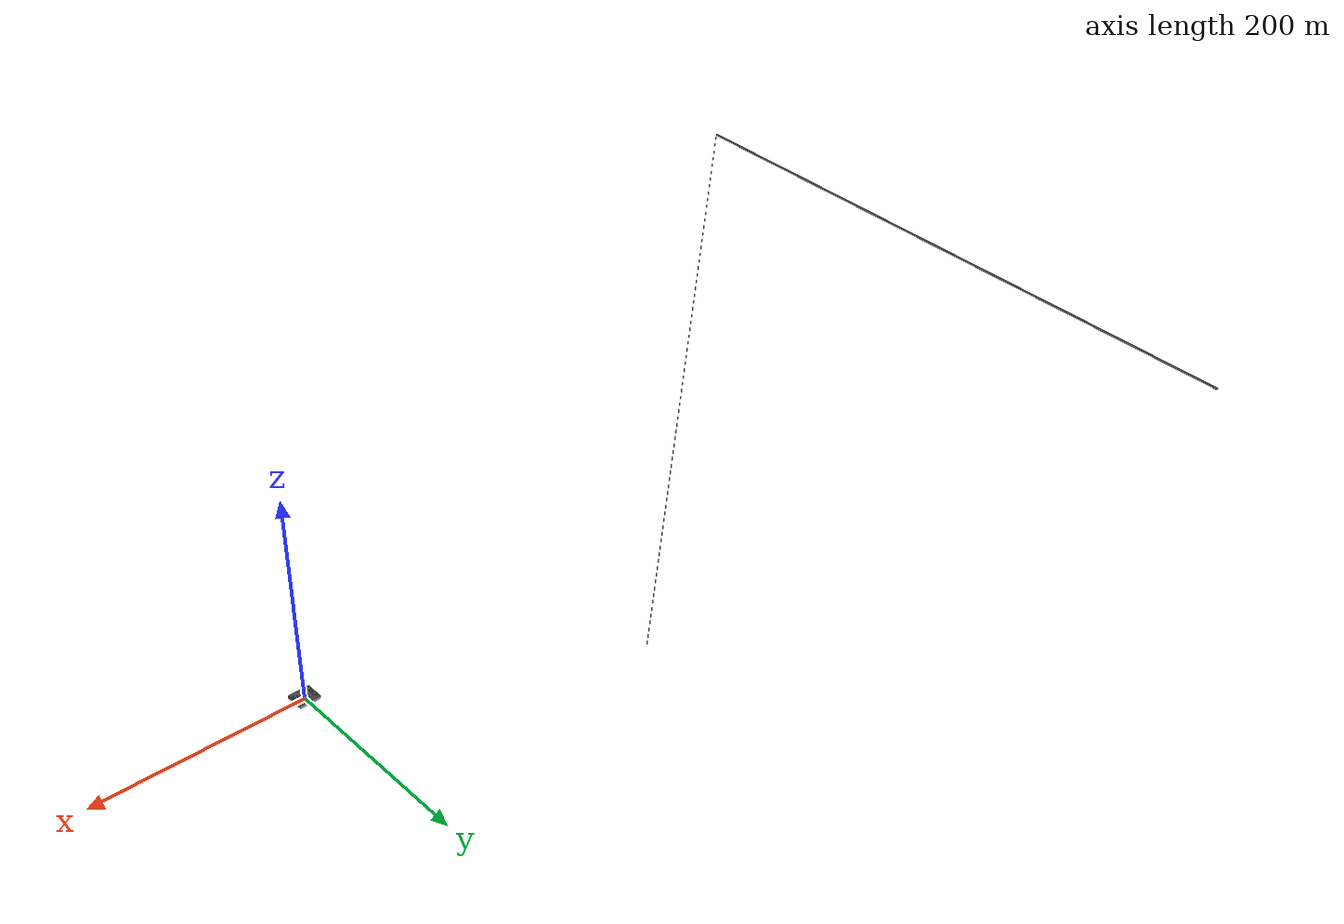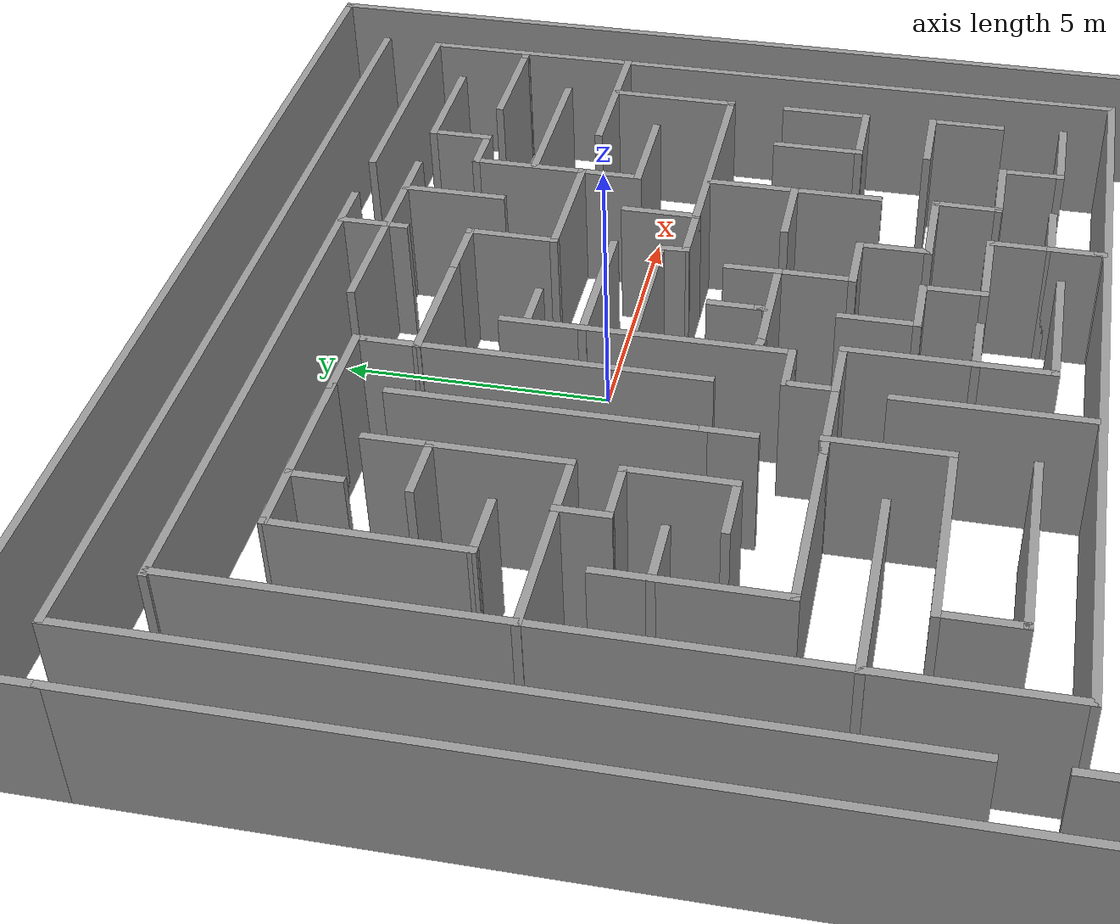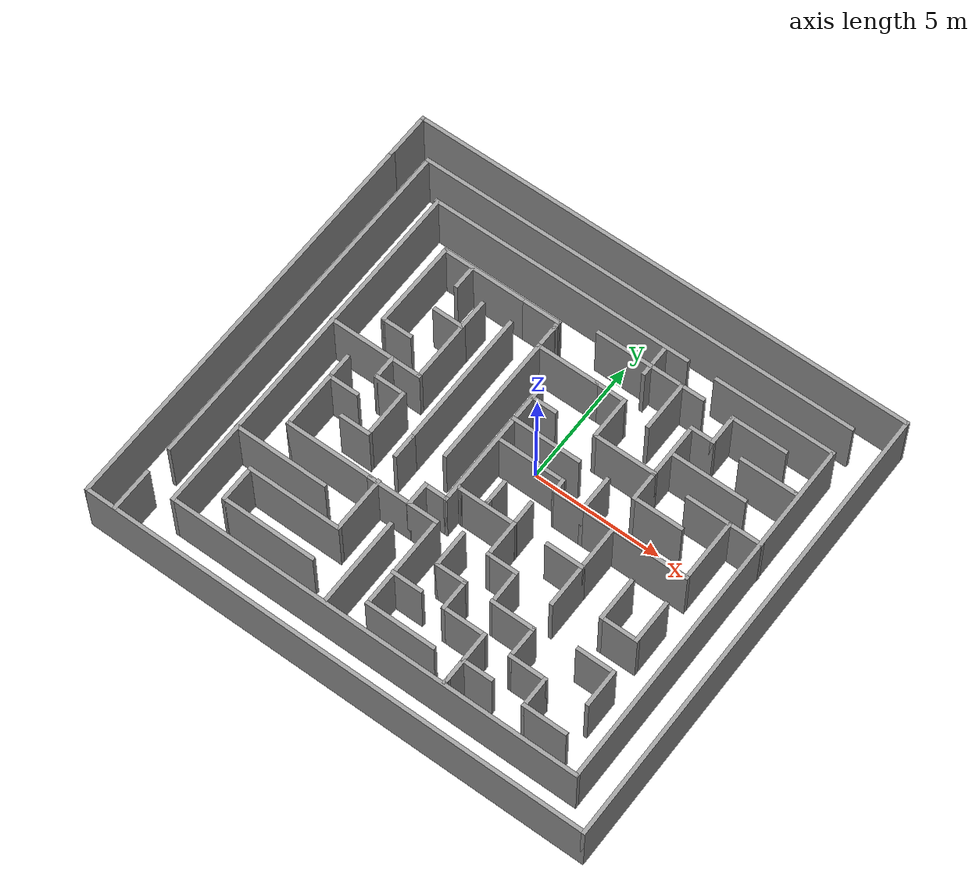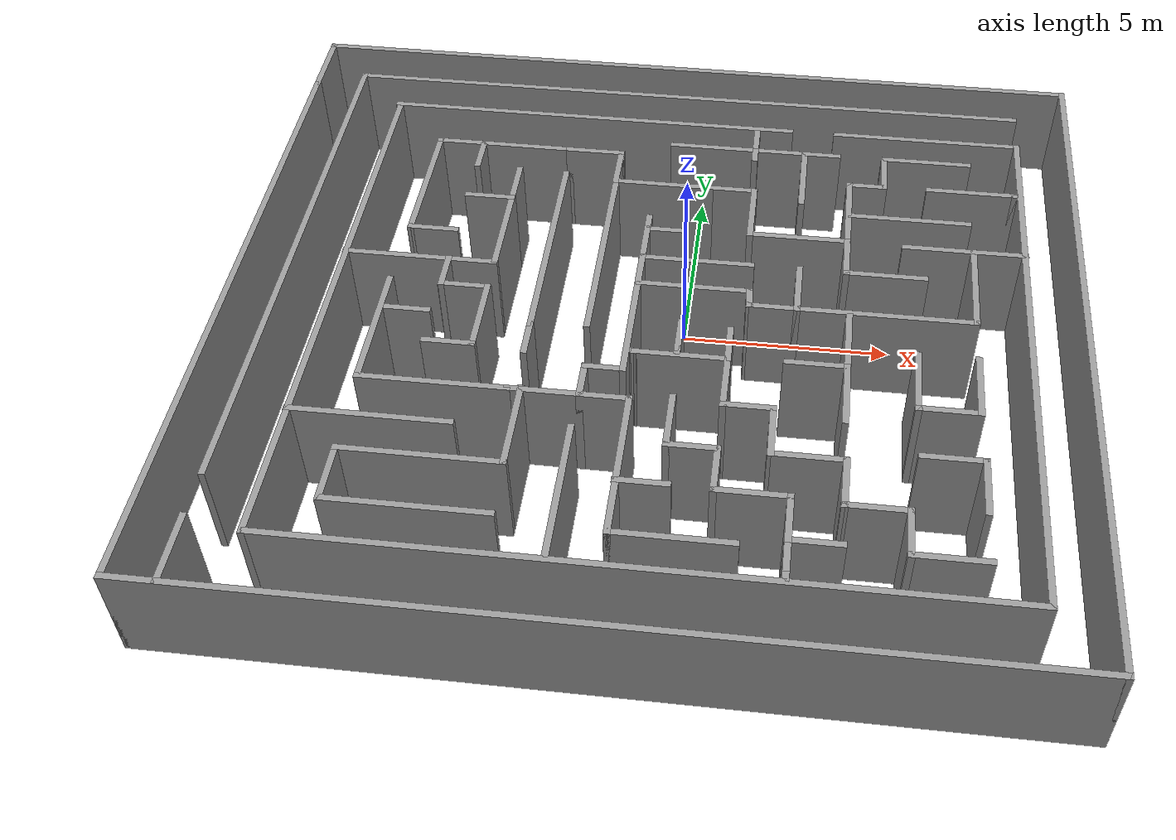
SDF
<?xml version='1.0'?>
<sdf version='1.7'>
  <model name='complicated_maze'>
    <pose>-467.07 -176.982 0 0 -0 0</pose>
    <link name='Wall_104'>
      <collision name='Wall_104_Collision'>
        <geometry>
          <box>
            <size>3.5 0.15 2.5</size>
          </box>
        </geometry>
        <pose>0 0 1.25 0 -0 0</pose>
      </collision>
      <visual name='Wall_104_Visual'>
        <pose>0 0 1.25 0 -0 0</pose>
        <geometry>
          <box>
            <size>3.5 0.15 2.5</size>
          </box>
        </geometry>
        <material>
          <script>
            <uri>file://media/materials/scripts/gazebo.material</uri>
            <name>Gazebo/Grey</name>
          </script>
          <ambient>1 1 1 1</ambient>
        </material>
        <meta>
          <layer>0</layer>
        </meta>
      </visual>
      <pose>461.998 180.966 0 0 -0 0</pose>
    </link>
    <link name='Wall_108'>
      <collision name='Wall_108_Collision'>
        <geometry>
          <box>
            <size>1.5 0.15 2.5</size>
          </box>
        </geometry>
        <pose>0 0 1.25 0 -0 0</pose>
      </collision>
      <visual name='Wall_108_Visual'>
        <pose>0 0 1.25 0 -0 0</pose>
        <geometry>
          <box>
            <size>1.5 0.15 2.5</size>
          </box>
        </geometry>
        <material>
          <script>
            <uri>file://media/materials/scripts/gazebo.material</uri>
            <name>Gazebo/Grey</name>
          </script>
          <ambient>1 1 1 1</ambient>
        </material>
        <meta>
          <layer>0</layer>
        </meta>
      </visual>
      <pose>464.348 180.966 0 0 -0 0</pose>
    </link>
    <link name='Wall_109'>
      <collision name='Wall_109_Collision'>
        <geometry>
          <box>
            <size>1.25004 0.15 2.5</size>
          </box>
        </geometry>
        <pose>0 0 1.25 0 -0 0</pose>
      </collision>
      <visual name='Wall_109_Visual'>
        <pose>0 0 1.25 0 -0 0</pose>
        <geometry>
          <box>
            <size>1.25004 0.15 2.5</size>
          </box>
        </geometry>
        <material>
          <script>
            <uri>file://media/materials/scripts/gazebo.material</uri>
            <name>Gazebo/Grey</name>
          </script>
          <ambient>1 1 1 1</ambient>
        </material>
        <meta>
          <layer>0</layer>
        </meta>
      </visual>
      <pose>465.02 180.416 0 0 -0 -1.57624</pose>
    </link>
    <link name='Wall_111'>
      <collision name='Wall_111_Collision'>
        <geometry>
          <box>
            <size>2.25 0.15 2.5</size>
          </box>
        </geometry>
        <pose>0 0 1.25 0 -0 0</pose>
      </collision>
      <visual name='Wall_111_Visual'>
        <pose>0 0 1.25 0 -0 0</pose>
        <geometry>
          <box>
            <size>2.25 0.15 2.5</size>
          </box>
        </geometry>
        <material>
          <script>
            <uri>file://media/materials/scripts/gazebo.material</uri>
            <name>Gazebo/Grey</name>
          </script>
          <ambient>1 1 1 1</ambient>
        </material>
        <meta>
          <layer>0</layer>
        </meta>
      </visual>
      <pose>467.369 181.458 0 0 -0 3.14159</pose>
    </link>
    <link name='Wall_113'>
      <collision name='Wall_113_Collision'>
        <geometry>
          <box>
            <size>5.25 0.15 2.5</size>
          </box>
        </geometry>
        <pose>0 0 1.25 0 -0 0</pose>
      </collision>
      <visual name='Wall_113_Visual'>
        <pose>0 0 1.25 0 -0 0</pose>
        <geometry>
          <box>
            <size>5.25 0.15 2.5</size>
          </box>
        </geometry>
        <material>
          <script>
            <uri>file://media/materials/scripts/gazebo.material</uri>
            <name>Gazebo/Grey</name>
          </script>
          <ambient>1 1 1 1</ambient>
        </material>
        <meta>
          <layer>0</layer>
        </meta>
      </visual>
      <pose>465.032 177.316 0 0 -0 -1.5708</pose>
    </link>
    <link name='Wall_115'>
      <collision name='Wall_115_Collision'>
        <geometry>
          <box>
            <size>5.5 0.15 2.5</size>
          </box>
        </geometry>
        <pose>0 0 1.25 0 -0 0</pose>
      </collision>
      <visual name='Wall_115_Visual'>
        <pose>0 0 1.25 0 -0 0</pose>
        <geometry>
          <box>
            <size>5.5 0.15 2.5</size>
          </box>
        </geometry>
        <material>
          <script>
            <uri>file://media/materials/scripts/gazebo.material</uri>
            <name>Gazebo/Grey</name>
          </script>
          <ambient>1 1 1 1</ambient>
        </material>
        <meta>
          <layer>0</layer>
        </meta>
      </visual>
      <pose>463.74 177.328 0 0 -0 -1.5708</pose>
    </link>
    <link name='Wall_117'>
      <collision name='Wall_117_Collision'>
        <geometry>
          <box>
            <size>1.75 0.15 2.5</size>
          </box>
        </geometry>
        <pose>0 0 1.25 0 -0 0</pose>
      </collision>
      <visual name='Wall_117_Visual'>
        <pose>0 0 1.25 0 -0 0</pose>
        <geometry>
          <box>
            <size>1.75 0.15 2.5</size>
          </box>
        </geometry>
        <material>
          <script>
            <uri>file://media/materials/scripts/gazebo.material</uri>
            <name>Gazebo/Grey</name>
          </script>
          <ambient>1 1 1 1</ambient>
        </material>
        <meta>
          <layer>0</layer>
        </meta>
      </visual>
      <pose>464.365 172.657 0 0 -0 0</pose>
    </link>
    <link name='Wall_118'>
      <collision name='Wall_118_Collision'>
        <geometry>
          <box>
            <size>1 0.15 2.5</size>
          </box>
        </geometry>
        <pose>0 0 1.25 0 -0 0</pose>
      </collision>
      <visual name='Wall_118_Visual'>
        <pose>0 0 1.25 0 -0 0</pose>
        <geometry>
          <box>
            <size>1 0.15 2.5</size>
          </box>
        </geometry>
        <material>
          <script>
            <uri>file://media/materials/scripts/gazebo.material</uri>
            <name>Gazebo/Grey</name>
          </script>
          <ambient>1 1 1 1</ambient>
        </material>
        <meta>
          <layer>0</layer>
        </meta>
      </visual>
      <pose>465.165 173.082 0 0 -0 1.5708</pose>
    </link>
    <link name='Wall_120'>
      <collision name='Wall_120_Collision'>
        <geometry>
          <box>
            <size>1 0.15 2.5</size>
          </box>
        </geometry>
        <pose>0 0 1.25 0 -0 0</pose>
      </collision>
      <visual name='Wall_120_Visual'>
        <pose>0 0 1.25 0 -0 0</pose>
        <geometry>
          <box>
            <size>1 0.15 2.5</size>
          </box>
        </geometry>
        <material>
          <script>
            <uri>file://media/materials/scripts/gazebo.material</uri>
            <name>Gazebo/Grey</name>
          </script>
          <ambient>1 1 1 1</ambient>
        </material>
        <meta>
          <layer>0</layer>
        </meta>
      </visual>
      <pose>463.74 174.228 0 0 -0 -1.5708</pose>
    </link>
    <link name='Wall_123'>
      <collision name='Wall_123_Collision'>
        <geometry>
          <box>
            <size>1 0.15 2.5</size>
          </box>
        </geometry>
        <pose>0 0 1.25 0 -0 0</pose>
      </collision>
      <visual name='Wall_123_Visual'>
        <pose>0 0 1.25 0 -0 0</pose>
        <geometry>
          <box>
            <size>1 0.15 2.5</size>
          </box>
        </geometry>
        <material>
          <script>
            <uri>file://media/materials/scripts/gazebo.material</uri>
            <name>Gazebo/Grey</name>
          </script>
          <ambient>1 1 1 1</ambient>
        </material>
        <meta>
          <layer>0</layer>
        </meta>
      </visual>
      <pose>465.59 173.507 0 0 -0 0</pose>
    </link>
    <link name='Wall_124'>
      <collision name='Wall_124_Collision'>
        <geometry>
          <box>
            <size>5.25 0.15 2.5</size>
          </box>
        </geometry>
        <pose>0 0 1.25 0 -0 0</pose>
      </collision>
      <visual name='Wall_124_Visual'>
        <pose>0 0 1.25 0 -0 0</pose>
        <geometry>
          <box>
            <size>5.25 0.15 2.5</size>
          </box>
        </geometry>
        <material>
          <script>
            <uri>file://media/materials/scripts/gazebo.material</uri>
            <name>Gazebo/Grey</name>
          </script>
          <ambient>1 1 1 1</ambient>
        </material>
        <meta>
          <layer>0</layer>
        </meta>
      </visual>
      <pose>466.015 176.057 0 0 -0 1.5708</pose>
    </link>
    <link name='Wall_126'>
      <collision name='Wall_126_Collision'>
        <geometry>
          <box>
            <size>1 0.15 2.5</size>
          </box>
        </geometry>
        <pose>0 0 1.25 0 -0 0</pose>
      </collision>
      <visual name='Wall_126_Visual'>
        <pose>0 0 1.25 0 -0 0</pose>
        <geometry>
          <box>
            <size>1 0.15 2.5</size>
          </box>
        </geometry>
        <material>
          <script>
            <uri>file://media/materials/scripts/gazebo.material</uri>
            <name>Gazebo/Grey</name>
          </script>
          <ambient>1 1 1 1</ambient>
        </material>
        <meta>
          <layer>0</layer>
        </meta>
      </visual>
      <pose>466.489 178.185 0 0 -0 0</pose>
    </link>
    <link name='Wall_130'>
      <collision name='Wall_130_Collision'>
        <geometry>
          <box>
            <size>2.75 0.15 2.5</size>
          </box>
        </geometry>
        <pose>0 0 1.25 0 -0 0</pose>
      </collision>
      <visual name='Wall_130_Visual'>
        <pose>0 0 1.25 0 -0 0</pose>
        <geometry>
          <box>
            <size>2.75 0.15 2.5</size>
          </box>
        </geometry>
        <material>
          <script>
            <uri>file://media/materials/scripts/gazebo.material</uri>
            <name>Gazebo/Grey</name>
          </script>
          <ambient>1 1 1 1</ambient>
        </material>
        <meta>
          <layer>0</layer>
        </meta>
      </visual>
      <pose>467.305 177.176 0 0 -0 0</pose>
    </link>
    <link name='Wall_132'>
      <collision name='Wall_132_Collision'>
        <geometry>
          <box>
            <size>2.75 0.15 2.5</size>
          </box>
        </geometry>
        <pose>0 0 1.25 0 -0 0</pose>
      </collision>
      <visual name='Wall_132_Visual'>
        <pose>0 0 1.25 0 -0 0</pose>
        <geometry>
          <box>
            <size>2.75 0.15 2.5</size>
          </box>
        </geometry>
        <material>
          <script>
            <uri>file://media/materials/scripts/gazebo.material</uri>
            <name>Gazebo/Grey</name>
          </script>
          <ambient>1 1 1 1</ambient>
        </material>
        <meta>
          <layer>0</layer>
        </meta>
      </visual>
      <pose>467.326 176.287 0 0 -0 0</pose>
    </link>
    <link name='Wall_136'>
      <collision name='Wall_136_Collision'>
        <geometry>
          <box>
            <size>1.25 0.15 2.5</size>
          </box>
        </geometry>
        <pose>0 0 1.25 0 -0 0</pose>
      </collision>
      <visual name='Wall_136_Visual'>
        <pose>0 0 1.25 0 -0 0</pose>
        <geometry>
          <box>
            <size>1.25 0.15 2.5</size>
          </box>
        </geometry>
        <material>
          <script>
            <uri>file://media/materials/scripts/gazebo.material</uri>
            <name>Gazebo/Grey</name>
          </script>
          <ambient>1 1 1 1</ambient>
        </material>
        <meta>
          <layer>0</layer>
        </meta>
      </visual>
      <pose>469.202 175.833 0 0 -0 3.14159</pose>
    </link>
    <link name='Wall_137'>
      <collision name='Wall_137_Collision'>
        <geometry>
          <box>
            <size>0.603934 0.15 2.5</size>
          </box>
        </geometry>
        <pose>0 0 1.25 0 -0 0</pose>
      </collision>
      <visual name='Wall_137_Visual'>
        <pose>0 0 1.25 0 -0 0</pose>
        <geometry>
          <box>
            <size>0.603934 0.15 2.5</size>
          </box>
        </geometry>
        <material>
          <script>
            <uri>file://media/materials/scripts/gazebo.material</uri>
            <name>Gazebo/Grey</name>
          </script>
          <ambient>1 1 1 1</ambient>
        </material>
        <meta>
          <layer>0</layer>
        </meta>
      </visual>
      <pose>468.639 176.06 0 0 -0 1.62768</pose>
    </link>
    <link name='Wall_139'>
      <collision name='Wall_139_Collision'>
        <geometry>
          <box>
            <size>1.75 0.15 2.5</size>
          </box>
        </geometry>
        <pose>0 0 1.25 0 -0 0</pose>
      </collision>
      <visual name='Wall_139_Visual'>
        <pose>0 0 1.25 0 -0 0</pose>
        <geometry>
          <box>
            <size>1.75 0.15 2.5</size>
          </box>
        </geometry>
        <material>
          <script>
            <uri>file://media/materials/scripts/gazebo.material</uri>
            <name>Gazebo/Grey</name>
          </script>
          <ambient>1 1 1 1</ambient>
        </material>
        <meta>
          <layer>0</layer>
        </meta>
      </visual>
      <pose>473.865 173.889 0 0 -0 -1.5708</pose>
    </link>
    <link name='Wall_140'>
      <collision name='Wall_140_Collision'>
        <geometry>
          <box>
            <size>1.5 0.15 2.5</size>
          </box>
        </geometry>
        <pose>0 0 1.25 0 -0 0</pose>
      </collision>
      <visual name='Wall_140_Visual'>
        <pose>0 0 1.25 0 -0 0</pose>
        <geometry>
          <box>
            <size>1.5 0.15 2.5</size>
          </box>
        </geometry>
        <material>
          <script>
            <uri>file://media/materials/scripts/gazebo.material</uri>
            <name>Gazebo/Grey</name>
          </script>
          <ambient>1 1 1 1</ambient>
        </material>
        <meta>
          <layer>0</layer>
        </meta>
      </visual>
      <pose>473.19 173.089 0 0 -0 3.14159</pose>
    </link>
    <link name='Wall_141'>
      <collision name='Wall_141_Collision'>
        <geometry>
          <box>
            <size>1.75 0.15 2.5</size>
          </box>
        </geometry>
        <pose>0 0 1.25 0 -0 0</pose>
      </collision>
      <visual name='Wall_141_Visual'>
        <pose>0 0 1.25 0 -0 0</pose>
        <geometry>
          <box>
            <size>1.75 0.15 2.5</size>
          </box>
        </geometry>
        <material>
          <script>
            <uri>file://media/materials/scripts/gazebo.material</uri>
            <name>Gazebo/Grey</name>
          </script>
          <ambient>1 1 1 1</ambient>
        </material>
        <meta>
          <layer>0</layer>
        </meta>
      </visual>
      <pose>472.515 173.889 0 0 -0 1.5708</pose>
    </link>
    <link name='Wall_143'>
      <collision name='Wall_143_Collision'>
        <geometry>
          <box>
            <size>1.5 0.15 2.5</size>
          </box>
        </geometry>
        <pose>0 0 1.25 0 -0 0</pose>
      </collision>
      <visual name='Wall_143_Visual'>
        <pose>0 0 1.25 0 -0 0</pose>
        <geometry>
          <box>
            <size>1.5 0.15 2.5</size>
          </box>
        </geometry>
        <material>
          <script>
            <uri>file://media/materials/scripts/gazebo.material</uri>
            <name>Gazebo/Grey</name>
          </script>
          <ambient>1 1 1 1</ambient>
        </material>
        <meta>
          <layer>0</layer>
        </meta>
      </visual>
      <pose>473.25 171.758 0 0 -0 0</pose>
    </link>
    <link name='Wall_144'>
      <collision name='Wall_144_Collision'>
        <geometry>
          <box>
            <size>1.5 0.15 2.5</size>
          </box>
        </geometry>
        <pose>0 0 1.25 0 -0 0</pose>
      </collision>
      <visual name='Wall_144_Visual'>
        <pose>0 0 1.25 0 -0 0</pose>
        <geometry>
          <box>
            <size>1.5 0.15 2.5</size>
          </box>
        </geometry>
        <material>
          <script>
            <uri>file://media/materials/scripts/gazebo.material</uri>
            <name>Gazebo/Grey</name>
          </script>
          <ambient>1 1 1 1</ambient>
        </material>
        <meta>
          <layer>0</layer>
        </meta>
      </visual>
      <pose>473.925 171.083 0 0 -0 -1.5708</pose>
    </link>
    <link name='Wall_147'>
      <collision name='Wall_147_Collision'>
        <geometry>
          <box>
            <size>1.75 0.15 2.5</size>
          </box>
        </geometry>
        <pose>0 0 1.25 0 -0 0</pose>
      </collision>
      <visual name='Wall_147_Visual'>
        <pose>0 0 1.25 0 -0 0</pose>
        <geometry>
          <box>
            <size>1.75 0.15 2.5</size>
          </box>
        </geometry>
        <material>
          <script>
            <uri>file://media/materials/scripts/gazebo.material</uri>
            <name>Gazebo/Grey</name>
          </script>
          <ambient>1 1 1 1</ambient>
        </material>
        <meta>
          <layer>0</layer>
        </meta>
      </visual>
      <pose>473.149 169.177 0 0 -0 3.14159</pose>
    </link>
    <link name='Wall_148'>
      <collision name='Wall_148_Collision'>
        <geometry>
          <box>
            <size>1.25 0.15 2.5</size>
          </box>
        </geometry>
        <pose>0 0 1.25 0 -0 0</pose>
      </collision>
      <visual name='Wall_148_Visual'>
        <pose>0 0 1.25 0 -0 0</pose>
        <geometry>
          <box>
            <size>1.25 0.15 2.5</size>
          </box>
        </geometry>
        <material>
          <script>
            <uri>file://media/materials/scripts/gazebo.material</uri>
            <name>Gazebo/Grey</name>
          </script>
          <ambient>1 1 1 1</ambient>
        </material>
        <meta>
          <layer>0</layer>
        </meta>
      </visual>
      <pose>472.349 169.727 0 0 -0 1.5708</pose>
    </link>
    <link name='Wall_149'>
      <collision name='Wall_149_Collision'>
        <geometry>
          <box>
            <size>1.5 0.15 2.5</size>
          </box>
        </geometry>
        <pose>0 0 1.25 0 -0 0</pose>
      </collision>
      <visual name='Wall_149_Visual'>
        <pose>0 0 1.25 0 -0 0</pose>
        <geometry>
          <box>
            <size>1.5 0.15 2.5</size>
          </box>
        </geometry>
        <material>
          <script>
            <uri>file://media/materials/scripts/gazebo.material</uri>
            <name>Gazebo/Grey</name>
          </script>
          <ambient>1 1 1 1</ambient>
        </material>
        <meta>
          <layer>0</layer>
        </meta>
      </visual>
      <pose>471.674 170.277 0 0 -0 3.14159</pose>
    </link>
    <link name='Wall_150'>
      <collision name='Wall_150_Collision'>
        <geometry>
          <box>
            <size>1.33389 0.15 2.5</size>
          </box>
        </geometry>
        <pose>0 0 1.25 0 -0 0</pose>
      </collision>
      <visual name='Wall_150_Visual'>
        <pose>0 0 1.25 0 -0 0</pose>
        <geometry>
          <box>
            <size>1.33389 0.15 2.5</size>
          </box>
        </geometry>
        <material>
          <script>
            <uri>file://media/materials/scripts/gazebo.material</uri>
            <name>Gazebo/Grey</name>
          </script>
          <ambient>1 1 1 1</ambient>
        </material>
        <meta>
          <layer>0</layer>
        </meta>
      </visual>
      <pose>471.006 170.869 0 0 -0 1.56</pose>
    </link>
    <link name='Wall_151'>
      <collision name='Wall_151_Collision'>
        <geometry>
          <box>
            <size>1.75 0.15 2.5</size>
          </box>
        </geometry>
        <pose>0 0 1.25 0 -0 0</pose>
      </collision>
      <visual name='Wall_151_Visual'>
        <pose>0 0 1.25 0 -0 0</pose>
        <geometry>
          <box>
            <size>1.75 0.15 2.5</size>
          </box>
        </geometry>
        <material>
          <script>
            <uri>file://media/materials/scripts/gazebo.material</uri>
            <name>Gazebo/Grey</name>
          </script>
          <ambient>1 1 1 1</ambient>
        </material>
        <meta>
          <layer>0</layer>
        </meta>
      </visual>
      <pose>470.199 171.461 0 0 -0 3.14159</pose>
    </link>
    <link name='Wall_152'>
      <collision name='Wall_152_Collision'>
        <geometry>
          <box>
            <size>1.41625 0.15 2.5</size>
          </box>
        </geometry>
        <pose>0 0 1.25 0 -0 0</pose>
      </collision>
      <visual name='Wall_152_Visual'>
        <pose>0 0 1.25 0 -0 0</pose>
        <geometry>
          <box>
            <size>1.41625 0.15 2.5</size>
          </box>
        </geometry>
        <material>
          <script>
            <uri>file://media/materials/scripts/gazebo.material</uri>
            <name>Gazebo/Grey</name>
          </script>
          <ambient>1 1 1 1</ambient>
        </material>
        <meta>
          <layer>0</layer>
        </meta>
      </visual>
      <pose>469.406 172.094 0 0 -0 1.58089</pose>
    </link>
    <link name='Wall_153'>
      <collision name='Wall_153_Collision'>
        <geometry>
          <box>
            <size>1.25 0.15 2.5</size>
          </box>
        </geometry>
        <pose>0 0 1.25 0 -0 0</pose>
      </collision>
      <visual name='Wall_153_Visual'>
        <pose>0 0 1.25 0 -0 0</pose>
        <geometry>
          <box>
            <size>1.25 0.15 2.5</size>
          </box>
        </geometry>
        <material>
          <script>
            <uri>file://media/materials/scripts/gazebo.material</uri>
            <name>Gazebo/Grey</name>
          </script>
          <ambient>1 1 1 1</ambient>
        </material>
        <meta>
          <layer>0</layer>
        </meta>
      </visual>
      <pose>468.849 172.727 0 0 -0 3.14159</pose>
    </link>
    <link name='Wall_154'>
      <collision name='Wall_154_Collision'>
        <geometry>
          <box>
            <size>1.5 0.15 2.5</size>
          </box>
        </geometry>
        <pose>0 0 1.25 0 -0 0</pose>
      </collision>
      <visual name='Wall_154_Visual'>
        <pose>0 0 1.25 0 -0 0</pose>
        <geometry>
          <box>
            <size>1.5 0.15 2.5</size>
          </box>
        </geometry>
        <material>
          <script>
            <uri>file://media/materials/scripts/gazebo.material</uri>
            <name>Gazebo/Grey</name>
          </script>
          <ambient>1 1 1 1</ambient>
        </material>
        <meta>
          <layer>0</layer>
        </meta>
      </visual>
      <pose>468.299 173.402 0 0 -0 1.5708</pose>
    </link>
    <link name='Wall_155'>
      <collision name='Wall_155_Collision'>
        <geometry>
          <box>
            <size>2.25 0.15 2.5</size>
          </box>
        </geometry>
        <pose>0 0 1.25 0 -0 0</pose>
      </collision>
      <visual name='Wall_155_Visual'>
        <pose>0 0 1.25 0 -0 0</pose>
        <geometry>
          <box>
            <size>2.25 0.15 2.5</size>
          </box>
        </geometry>
        <material>
          <script>
            <uri>file://media/materials/scripts/gazebo.material</uri>
            <name>Gazebo/Grey</name>
          </script>
          <ambient>1 1 1 1</ambient>
        </material>
        <meta>
          <layer>0</layer>
        </meta>
      </visual>
      <pose>467.249 174.077 0 0 -0 3.14159</pose>
    </link>
    <link name='Wall_156'>
      <collision name='Wall_156_Collision'>
        <geometry>
          <box>
            <size>0.25 0.15 2.5</size>
          </box>
        </geometry>
        <pose>0 0 1.25 0 -0 0</pose>
      </collision>
      <visual name='Wall_156_Visual'>
        <pose>0 0 1.25 0 -0 0</pose>
        <geometry>
          <box>
            <size>0.25 0.15 2.5</size>
          </box>
        </geometry>
        <material>
          <script>
            <uri>file://media/materials/scripts/gazebo.material</uri>
            <name>Gazebo/Grey</name>
          </script>
          <ambient>1 1 1 1</ambient>
        </material>
        <meta>
          <layer>0</layer>
        </meta>
      </visual>
      <pose>466.151 174.09 0 0 -0 2.87979</pose>
    </link>
    <link name='Wall_158'>
      <collision name='Wall_158_Collision'>
        <geometry>
          <box>
            <size>1.07287 0.15 2.5</size>
          </box>
        </geometry>
        <pose>0 0 1.25 0 -0 0</pose>
      </collision>
      <visual name='Wall_158_Visual'>
        <pose>0 0 1.25 0 -0 0</pose>
        <geometry>
          <box>
            <size>1.07287 0.15 2.5</size>
          </box>
        </geometry>
        <material>
          <script>
            <uri>file://media/materials/scripts/gazebo.material</uri>
            <name>Gazebo/Grey</name>
          </script>
          <ambient>1 1 1 1</ambient>
        </material>
        <meta>
          <layer>0</layer>
        </meta>
      </visual>
      <pose>468.294 174.539 0 0 -0 -1.55921</pose>
    </link>
    <link name='Wall_16'>
      <collision name='Wall_16_Collision'>
        <geometry>
          <box>
            <size>16.25 0.15 2.5</size>
          </box>
        </geometry>
        <pose>0 0 1.25 0 -0 0</pose>
      </collision>
      <visual name='Wall_16_Visual'>
        <pose>0 0 1.25 0 -0 0</pose>
        <geometry>
          <box>
            <size>16.25 0.15 2.5</size>
          </box>
        </geometry>
        <material>
          <script>
            <uri>file://media/materials/scripts/gazebo.material</uri>
            <name>Gazebo/Grey</name>
          </script>
          <ambient>1 1 1 1</ambient>
        </material>
        <meta>
          <layer>0</layer>
        </meta>
      </visual>
      <pose>456.517 174.907 0 0 -0 -1.5708</pose>
    </link>
    <link name='Wall_160'>
      <collision name='Wall_160_Collision'>
        <geometry>
          <box>
            <size>1 0.15 2.5</size>
          </box>
        </geometry>
        <pose>0 0 1.25 0 -0 0</pose>
      </collision>
      <visual name='Wall_160_Visual'>
        <pose>0 0 1.25 0 -0 0</pose>
        <geometry>
          <box>
            <size>1 0.15 2.5</size>
          </box>
        </geometry>
        <material>
          <script>
            <uri>file://media/materials/scripts/gazebo.material</uri>
            <name>Gazebo/Grey</name>
          </script>
          <ambient>1 1 1 1</ambient>
        </material>
        <meta>
          <layer>0</layer>
        </meta>
      </visual>
      <pose>467.15 174.69 0 0 -0 -1.5708</pose>
    </link>
    <link name='Wall_161'>
      <collision name='Wall_161_Collision'>
        <geometry>
          <box>
            <size>0.25 0.15 2.5</size>
          </box>
        </geometry>
        <pose>0 0 1.25 0 -0 0</pose>
      </collision>
      <visual name='Wall_161_Visual'>
        <pose>0 0 1.25 0 -0 0</pose>
        <geometry>
          <box>
            <size>0.25 0.15 2.5</size>
          </box>
        </geometry>
        <material>
          <script>
            <uri>file://media/materials/scripts/gazebo.material</uri>
            <name>Gazebo/Grey</name>
          </script>
          <ambient>1 1 1 1</ambient>
        </material>
        <meta>
          <layer>0</layer>
        </meta>
      </visual>
      <pose>467.15 174.215 0 0 -0 -1.5708</pose>
    </link>
    <link name='Wall_163'>
      <collision name='Wall_163_Collision'>
        <geometry>
          <box>
            <size>1.5 0.15 2.5</size>
          </box>
        </geometry>
        <pose>0 0 1.25 0 -0 0</pose>
      </collision>
      <visual name='Wall_163_Visual'>
        <pose>0 0 1.25 0 -0 0</pose>
        <geometry>
          <box>
            <size>1.5 0.15 2.5</size>
          </box>
        </geometry>
        <material>
          <script>
            <uri>file://media/materials/scripts/gazebo.material</uri>
            <name>Gazebo/Grey</name>
          </script>
          <ambient>1 1 1 1</ambient>
        </material>
        <meta>
          <layer>0</layer>
        </meta>
      </visual>
      <pose>470.282 174.142 0 0 -0 0</pose>
    </link>
    <link name='Wall_164'>
      <collision name='Wall_164_Collision'>
        <geometry>
          <box>
            <size>1.75 0.15 2.5</size>
          </box>
        </geometry>
        <pose>0 0 1.25 0 -0 0</pose>
      </collision>
      <visual name='Wall_164_Visual'>
        <pose>0 0 1.25 0 -0 0</pose>
        <geometry>
          <box>
            <size>1.75 0.15 2.5</size>
          </box>
        </geometry>
        <material>
          <script>
            <uri>file://media/materials/scripts/gazebo.material</uri>
            <name>Gazebo/Grey</name>
          </script>
          <ambient>1 1 1 1</ambient>
        </material>
        <meta>
          <layer>0</layer>
        </meta>
      </visual>
      <pose>470.957 174.942 0 0 -0 1.5708</pose>
    </link>
    <link name='Wall_166'>
      <collision name='Wall_166_Collision'>
        <geometry>
          <box>
            <size>1.75 0.15 2.5</size>
          </box>
        </geometry>
        <pose>0 0 1.25 0 -0 0</pose>
      </collision>
      <visual name='Wall_166_Visual'>
        <pose>0 0 1.25 0 -0 0</pose>
        <geometry>
          <box>
            <size>1.75 0.15 2.5</size>
          </box>
        </geometry>
        <material>
          <script>
            <uri>file://media/materials/scripts/gazebo.material</uri>
            <name>Gazebo/Grey</name>
          </script>
          <ambient>1 1 1 1</ambient>
        </material>
        <meta>
          <layer>0</layer>
        </meta>
      </visual>
      <pose>470.957 173.342 0 0 -0 -1.5708</pose>
    </link>
    <link name='Wall_168'>
      <collision name='Wall_168_Collision'>
        <geometry>
          <box>
            <size>1.25 0.15 2.5</size>
          </box>
        </geometry>
        <pose>0 0 1.25 0 -0 0</pose>
      </collision>
      <visual name='Wall_168_Visual'>
        <pose>0 0 1.25 0 -0 0</pose>
        <geometry>
          <box>
            <size>1.25 0.15 2.5</size>
          </box>
        </geometry>
        <material>
          <script>
            <uri>file://media/materials/scripts/gazebo.material</uri>
            <name>Gazebo/Grey</name>
          </script>
          <ambient>1 1 1 1</ambient>
        </material>
        <meta>
          <layer>0</layer>
        </meta>
      </visual>
      <pose>470.446 169.268 0 0 -0 3.14159</pose>
    </link>
    <link name='Wall_169'>
      <collision name='Wall_169_Collision'>
        <geometry>
          <box>
            <size>1.25 0.15 2.5</size>
          </box>
        </geometry>
        <pose>0 0 1.25 0 -0 0</pose>
      </collision>
      <visual name='Wall_169_Visual'>
        <pose>0 0 1.25 0 -0 0</pose>
        <geometry>
          <box>
            <size>1.25 0.15 2.5</size>
          </box>
        </geometry>
        <material>
          <script>
            <uri>file://media/materials/scripts/gazebo.material</uri>
            <name>Gazebo/Grey</name>
          </script>
          <ambient>1 1 1 1</ambient>
        </material>
        <meta>
          <layer>0</layer>
        </meta>
      </visual>
      <pose>469.896 169.818 0 0 -0 1.5708</pose>
    </link>
    <link name='Wall_17'>
      <collision name='Wall_17_Collision'>
        <geometry>
          <box>
            <size>20 0.15 2.5</size>
          </box>
        </geometry>
        <pose>0 0 1.25 0 -0 0</pose>
      </collision>
      <visual name='Wall_17_Visual'>
        <pose>0 0 1.25 0 -0 0</pose>
        <geometry>
          <box>
            <size>20 0.15 2.5</size>
          </box>
        </geometry>
        <material>
          <script>
            <uri>file://media/materials/scripts/gazebo.material</uri>
            <name>Gazebo/Grey</name>
          </script>
          <ambient>1 1 1 1</ambient>
        </material>
        <meta>
          <layer>0</layer>
        </meta>
      </visual>
      <pose>466.442 166.857 0 0 -0 0</pose>
    </link>
    <link name='Wall_170'>
      <collision name='Wall_170_Collision'>
        <geometry>
          <box>
            <size>1.75 0.15 2.5</size>
          </box>
        </geometry>
        <pose>0 0 1.25 0 -0 0</pose>
      </collision>
      <visual name='Wall_170_Visual'>
        <pose>0 0 1.25 0 -0 0</pose>
        <geometry>
          <box>
            <size>1.75 0.15 2.5</size>
          </box>
        </geometry>
        <material>
          <script>
            <uri>file://media/materials/scripts/gazebo.material</uri>
            <name>Gazebo/Grey</name>
          </script>
          <ambient>1 1 1 1</ambient>
        </material>
        <meta>
          <layer>0</layer>
        </meta>
      </visual>
      <pose>469.096 170.368 0 0 -0 3.14159</pose>
    </link>
    <link name='Wall_171'>
      <collision name='Wall_171_Collision'>
        <geometry>
          <box>
            <size>1.25 0.15 2.5</size>
          </box>
        </geometry>
        <pose>0 0 1.25 0 -0 0</pose>
      </collision>
      <visual name='Wall_171_Visual'>
        <pose>0 0 1.25 0 -0 0</pose>
        <geometry>
          <box>
            <size>1.25 0.15 2.5</size>
          </box>
        </geometry>
        <material>
          <script>
            <uri>file://media/materials/scripts/gazebo.material</uri>
            <name>Gazebo/Grey</name>
          </script>
          <ambient>1 1 1 1</ambient>
        </material>
        <meta>
          <layer>0</layer>
        </meta>
      </visual>
      <pose>468.296 170.918 0 0 -0 1.5708</pose>
    </link>
    <link name='Wall_172'>
      <collision name='Wall_172_Collision'>
        <geometry>
          <box>
            <size>1.25 0.15 2.5</size>
          </box>
        </geometry>
        <pose>0 0 1.25 0 -0 0</pose>
      </collision>
      <visual name='Wall_172_Visual'>
        <pose>0 0 1.25 0 -0 0</pose>
        <geometry>
          <box>
            <size>1.25 0.15 2.5</size>
          </box>
        </geometry>
        <material>
          <script>
            <uri>file://media/materials/scripts/gazebo.material</uri>
            <name>Gazebo/Grey</name>
          </script>
          <ambient>1 1 1 1</ambient>
        </material>
        <meta>
          <layer>0</layer>
        </meta>
      </visual>
      <pose>467.746 171.468 0 0 -0 3.14159</pose>
    </link>
    <link name='Wall_173'>
      <collision name='Wall_173_Collision'>
        <geometry>
          <box>
            <size>1.5 0.15 2.5</size>
          </box>
        </geometry>
        <pose>0 0 1.25 0 -0 0</pose>
      </collision>
      <visual name='Wall_173_Visual'>
        <pose>0 0 1.25 0 -0 0</pose>
        <geometry>
          <box>
            <size>1.5 0.15 2.5</size>
          </box>
        </geometry>
        <material>
          <script>
            <uri>file://media/materials/scripts/gazebo.material</uri>
            <name>Gazebo/Grey</name>
          </script>
          <ambient>1 1 1 1</ambient>
        </material>
        <meta>
          <layer>0</layer>
        </meta>
      </visual>
      <pose>467.196 172.143 0 0 -0 1.5708</pose>
    </link>
    <link name='Wall_177'>
      <collision name='Wall_177_Collision'>
        <geometry>
          <box>
            <size>1 0.15 2.5</size>
          </box>
        </geometry>
        <pose>0 0 1.25 0 -0 0</pose>
      </collision>
      <visual name='Wall_177_Visual'>
        <pose>0 0 1.25 0 -0 0</pose>
        <geometry>
          <box>
            <size>1 0.15 2.5</size>
          </box>
        </geometry>
        <material>
          <script>
            <uri>file://media/materials/scripts/gazebo.material</uri>
            <name>Gazebo/Grey</name>
          </script>
          <ambient>1 1 1 1</ambient>
        </material>
        <meta>
          <layer>0</layer>
        </meta>
      </visual>
      <pose>469.896 168.843 0 0 -0 -1.5708</pose>
    </link>
    <link name='Wall_178'>
      <collision name='Wall_178_Collision'>
        <geometry>
          <box>
            <size>0.25 0.15 2.5</size>
          </box>
        </geometry>
        <pose>0 0 1.25 0 -0 0</pose>
      </collision>
      <visual name='Wall_178_Visual'>
        <pose>0 0 1.25 0 -0 0</pose>
        <geometry>
          <box>
            <size>0.25 0.15 2.5</size>
          </box>
        </geometry>
        <material>
          <script>
            <uri>file://media/materials/scripts/gazebo.material</uri>
            <name>Gazebo/Grey</name>
          </script>
          <ambient>1 1 1 1</ambient>
        </material>
        <meta>
          <layer>0</layer>
        </meta>
      </visual>
      <pose>469.896 168.368 0 0 -0 -1.5708</pose>
    </link>
    <link name='Wall_18'>
      <collision name='Wall_18_Collision'>
        <geometry>
          <box>
            <size>18 0.15 2.5</size>
          </box>
        </geometry>
        <pose>0 0 1.25 0 -0 0</pose>
      </collision>
      <visual name='Wall_18_Visual'>
        <pose>0 0 1.25 0 -0 0</pose>
        <geometry>
          <box>
            <size>18 0.15 2.5</size>
          </box>
        </geometry>
        <material>
          <script>
            <uri>file://media/materials/scripts/gazebo.material</uri>
            <name>Gazebo/Grey</name>
          </script>
          <ambient>1 1 1 1</ambient>
        </material>
        <meta>
          <layer>0</layer>
        </meta>
      </visual>
      <pose>476.367 175.782 0 0 -0 1.5708</pose>
    </link>
    <link name='Wall_182'>
      <collision name='Wall_182_Collision'>
        <geometry>
          <box>
            <size>3.5 0.15 2.5</size>
          </box>
        </geometry>
        <pose>0 0 1.25 0 -0 0</pose>
      </collision>
      <visual name='Wall_182_Visual'>
        <pose>0 0 1.25 0 -0 0</pose>
        <geometry>
          <box>
            <size>3.5 0.15 2.5</size>
          </box>
        </geometry>
        <material>
          <script>
            <uri>file://media/materials/scripts/gazebo.material</uri>
            <name>Gazebo/Grey</name>
          </script>
          <ambient>1 1 1 1</ambient>
        </material>
        <meta>
          <layer>0</layer>
        </meta>
      </visual>
      <pose>465.126 170.035 0 0 -0 -1.5708</pose>
    </link>
    <link name='Wall_184'>
      <collision name='Wall_184_Collision'>
        <geometry>
          <box>
            <size>1.25 0.15 2.5</size>
          </box>
        </geometry>
        <pose>0 0 1.25 0 -0 0</pose>
      </collision>
      <visual name='Wall_184_Visual'>
        <pose>0 0 1.25 0 -0 0</pose>
        <geometry>
          <box>
            <size>1.25 0.15 2.5</size>
          </box>
        </geometry>
        <material>
          <script>
            <uri>file://media/materials/scripts/gazebo.material</uri>
            <name>Gazebo/Grey</name>
          </script>
          <ambient>1 1 1 1</ambient>
        </material>
        <meta>
          <layer>0</layer>
        </meta>
      </visual>
      <pose>465.715 172.657 0 0 -0 0</pose>
    </link>
    <link name='Wall_185'>
      <collision name='Wall_185_Collision'>
        <geometry>
          <box>
            <size>3.75 0.15 2.5</size>
          </box>
        </geometry>
        <pose>0 0 1.25 0 -0 0</pose>
      </collision>
      <visual name='Wall_185_Visual'>
        <pose>0 0 1.25 0 -0 0</pose>
        <geometry>
          <box>
            <size>3.75 0.15 2.5</size>
          </box>
        </geometry>
        <material>
          <script>
            <uri>file://media/materials/scripts/gazebo.material</uri>
            <name>Gazebo/Grey</name>
          </script>
          <ambient>1 1 1 1</ambient>
        </material>
        <meta>
          <layer>0</layer>
        </meta>
      </visual>
      <pose>466.265 170.857 0 0 -0 -1.5708</pose>
    </link>
    <link name='Wall_187'>
      <collision name='Wall_187_Collision'>
        <geometry>
          <box>
            <size>1.25 0.15 2.5</size>
          </box>
        </geometry>
        <pose>0 0 1.25 0 -0 0</pose>
      </collision>
      <visual name='Wall_187_Visual'>
        <pose>0 0 1.25 0 -0 0</pose>
        <geometry>
          <box>
            <size>1.25 0.15 2.5</size>
          </box>
        </geometry>
        <material>
          <script>
            <uri>file://media/materials/scripts/gazebo.material</uri>
            <name>Gazebo/Grey</name>
          </script>
          <ambient>1 1 1 1</ambient>
        </material>
        <meta>
          <layer>0</layer>
        </meta>
      </visual>
      <pose>466.8 170.395 0 0 -0 0</pose>
    </link>
    <link name='Wall_189'>
      <collision name='Wall_189_Collision'>
        <geometry>
          <box>
            <size>2.75 0.15 2.5</size>
          </box>
        </geometry>
        <pose>0 0 1.25 0 -0 0</pose>
      </collision>
      <visual name='Wall_189_Visual'>
        <pose>0 0 1.25 0 -0 0</pose>
        <geometry>
          <box>
            <size>2.75 0.15 2.5</size>
          </box>
        </geometry>
        <material>
          <script>
            <uri>file://media/materials/scripts/gazebo.material</uri>
            <name>Gazebo/Grey</name>
          </script>
          <ambient>1 1 1 1</ambient>
        </material>
        <meta>
          <layer>0</layer>
        </meta>
      </visual>
      <pose>467.565 169.057 0 0 -0 0</pose>
    </link>
    <link name='Wall_19'>
      <collision name='Wall_19_Collision'>
        <geometry>
          <box>
            <size>20 0.15 2.5</size>
          </box>
        </geometry>
        <pose>0 0 1.25 0 -0 0</pose>
      </collision>
      <visual name='Wall_19_Visual'>
        <pose>0 0 1.25 0 -0 0</pose>
        <geometry>
          <box>
            <size>20 0.15 2.5</size>
          </box>
        </geometry>
        <material>
          <script>
            <uri>file://media/materials/scripts/gazebo.material</uri>
            <name>Gazebo/Grey</name>
          </script>
          <ambient>1 1 1 1</ambient>
        </material>
        <meta>
          <layer>0</layer>
        </meta>
      </visual>
      <pose>466.442 184.707 0 0 -0 3.14159</pose>
    </link>
    <link name='Wall_193'>
      <collision name='Wall_193_Collision'>
        <geometry>
          <box>
            <size>2.25 0.15 2.5</size>
          </box>
        </geometry>
        <pose>0 0 1.25 0 -0 0</pose>
      </collision>
      <visual name='Wall_193_Visual'>
        <pose>0 0 1.25 0 -0 0</pose>
        <geometry>
          <box>
            <size>2.25 0.15 2.5</size>
          </box>
        </geometry>
        <material>
          <script>
            <uri>file://media/materials/scripts/gazebo.material</uri>
            <name>Gazebo/Grey</name>
          </script>
          <ambient>1 1 1 1</ambient>
        </material>
        <meta>
          <layer>0</layer>
        </meta>
      </visual>
      <pose>463.87 171.64 0 0 -0 -1.5708</pose>
    </link>
    <link name='Wall_194'>
      <collision name='Wall_194_Collision'>
        <geometry>
          <box>
            <size>3.75 0.15 2.5</size>
          </box>
        </geometry>
        <pose>0 0 1.25 0 -0 0</pose>
      </collision>
      <visual name='Wall_194_Visual'>
        <pose>0 0 1.25 0 -0 0</pose>
        <geometry>
          <box>
            <size>3.75 0.15 2.5</size>
          </box>
        </geometry>
        <material>
          <script>
            <uri>file://media/materials/scripts/gazebo.material</uri>
            <name>Gazebo/Grey</name>
          </script>
          <ambient>1 1 1 1</ambient>
        </material>
        <meta>
          <layer>0</layer>
        </meta>
      </visual>
      <pose>462.07 170.59 0 0 -0 3.14159</pose>
    </link>
    <link name='Wall_195'>
      <collision name='Wall_195_Collision'>
        <geometry>
          <box>
            <size>1.5 0.15 2.5</size>
          </box>
        </geometry>
        <pose>0 0 1.25 0 -0 0</pose>
      </collision>
      <visual name='Wall_195_Visual'>
        <pose>0 0 1.25 0 -0 0</pose>
        <geometry>
          <box>
            <size>1.5 0.15 2.5</size>
          </box>
        </geometry>
        <material>
          <script>
            <uri>file://media/materials/scripts/gazebo.material</uri>
            <name>Gazebo/Grey</name>
          </script>
          <ambient>1 1 1 1</ambient>
        </material>
        <meta>
          <layer>0</layer>
        </meta>
      </visual>
      <pose>460.27 169.915 0 0 -0 -1.5708</pose>
    </link>
    <link name='Wall_196'>
      <collision name='Wall_196_Collision'>
        <geometry>
          <box>
            <size>3.75 0.15 2.5</size>
          </box>
        </geometry>
        <pose>0 0 1.25 0 -0 0</pose>
      </collision>
      <visual name='Wall_196_Visual'>
        <pose>0 0 1.25 0 -0 0</pose>
        <geometry>
          <box>
            <size>3.75 0.15 2.5</size>
          </box>
        </geometry>
        <material>
          <script>
            <uri>file://media/materials/scripts/gazebo.material</uri>
            <name>Gazebo/Grey</name>
          </script>
          <ambient>1 1 1 1</ambient>
        </material>
        <meta>
          <layer>0</layer>
        </meta>
      </visual>
      <pose>462.07 169.24 0 0 -0 0</pose>
    </link>
    <link name='Wall_198'>
      <collision name='Wall_198_Collision'>
        <geometry>
          <box>
            <size>3.75 0.15 2.5</size>
          </box>
        </geometry>
        <pose>0 0 1.25 0 -0 0</pose>
      </collision>
      <visual name='Wall_198_Visual'>
        <pose>0 0 1.25 0 -0 0</pose>
        <geometry>
          <box>
            <size>3.75 0.15 2.5</size>
          </box>
        </geometry>
        <material>
          <script>
            <uri>file://media/materials/scripts/gazebo.material</uri>
            <name>Gazebo/Grey</name>
          </script>
          <ambient>1 1 1 1</ambient>
        </material>
        <meta>
          <layer>0</layer>
        </meta>
      </visual>
      <pose>460.744 171.552 0 0 -0 0</pose>
    </link>
    <link name='Wall_20'>
      <collision name='Wall_20_Collision'>
        <geometry>
          <box>
            <size>1.9 0.15 2.5</size>
          </box>
        </geometry>
        <pose>0 0 1.25 0 -0 0</pose>
      </collision>
      <visual name='Wall_20_Visual'>
        <pose>0 0 1.25 0 -0 0</pose>
        <geometry>
          <box>
            <size>1.9 0.15 2.5</size>
          </box>
        </geometry>
        <material>
          <script>
            <uri>file://media/materials/scripts/gazebo.material</uri>
            <name>Gazebo/Grey</name>
          </script>
          <ambient>1 1 1 1</ambient>
        </material>
        <meta>
          <layer>0</layer>
        </meta>
      </visual>
      <pose>456.517 183.832 0 0 -0 -1.5708</pose>
    </link>
    <link name='Wall_22'>
      <collision name='Wall_22_Collision'>
        <geometry>
          <box>
            <size>14 0.15 2.5</size>
          </box>
        </geometry>
        <pose>0 0 1.25 0 -0 0</pose>
      </collision>
      <visual name='Wall_22_Visual'>
        <pose>0 0 1.25 0 -0 0</pose>
        <geometry>
          <box>
            <size>14 0.15 2.5</size>
          </box>
        </geometry>
        <material>
          <script>
            <uri>file://media/materials/scripts/gazebo.material</uri>
            <name>Gazebo/Grey</name>
          </script>
          <ambient>1 1 1 1</ambient>
        </material>
        <meta>
          <layer>0</layer>
        </meta>
      </visual>
      <pose>457.697 176.54 0 0 -0 1.5708</pose>
    </link>
    <link name='Wall_23'>
      <collision name='Wall_23_Collision'>
        <geometry>
          <box>
            <size>17.5 0.15 2.5</size>
          </box>
        </geometry>
        <pose>0 0 1.25 0 -0 0</pose>
      </collision>
      <visual name='Wall_23_Visual'>
        <pose>0 0 1.25 0 -0 0</pose>
        <geometry>
          <box>
            <size>17.5 0.15 2.5</size>
          </box>
        </geometry>
        <material>
          <script>
            <uri>file://media/materials/scripts/gazebo.material</uri>
            <name>Gazebo/Grey</name>
          </script>
          <ambient>1 1 1 1</ambient>
        </material>
        <meta>
          <layer>0</layer>
        </meta>
      </visual>
      <pose>466.372 183.465 0 0 -0 0</pose>
    </link>
    <link name='Wall_25'>
      <collision name='Wall_25_Collision'>
        <geometry>
          <box>
            <size>1.75 0.15 2.5</size>
          </box>
        </geometry>
        <pose>0 0 1.25 0 -0 0</pose>
      </collision>
      <visual name='Wall_25_Visual'>
        <pose>0 0 1.25 0 -0 0</pose>
        <geometry>
          <box>
            <size>1.75 0.15 2.5</size>
          </box>
        </geometry>
        <material>
          <script>
            <uri>file://media/materials/scripts/gazebo.material</uri>
            <name>Gazebo/Grey</name>
          </script>
          <ambient>1 1 1 1</ambient>
        </material>
        <meta>
          <layer>0</layer>
        </meta>
      </visual>
      <pose>457.663 167.674 0 0 -0 -1.5708</pose>
    </link>
    <link name='Wall_27'>
      <collision name='Wall_27_Collision'>
        <geometry>
          <box>
            <size>10.5 0.15 2.5</size>
          </box>
        </geometry>
        <pose>0 0 1.25 0 -0 0</pose>
      </collision>
      <visual name='Wall_27_Visual'>
        <pose>0 0 1.25 0 -0 0</pose>
        <geometry>
          <box>
            <size>10.5 0.15 2.5</size>
          </box>
        </geometry>
        <material>
          <script>
            <uri>file://media/materials/scripts/gazebo.material</uri>
            <name>Gazebo/Grey</name>
          </script>
          <ambient>1 1 1 1</ambient>
        </material>
        <meta>
          <layer>0</layer>
        </meta>
      </visual>
      <pose>464.083 182.343 0 0 -0 0</pose>
    </link>
    <link name='Wall_29'>
      <collision name='Wall_29_Collision'>
        <geometry>
          <box>
            <size>4.75 0.15 2.5</size>
          </box>
        </geometry>
        <pose>0 0 1.25 0 -0 0</pose>
      </collision>
      <visual name='Wall_29_Visual'>
        <pose>0 0 1.25 0 -0 0</pose>
        <geometry>
          <box>
            <size>4.75 0.15 2.5</size>
          </box>
        </geometry>
        <material>
          <script>
            <uri>file://media/materials/scripts/gazebo.material</uri>
            <name>Gazebo/Grey</name>
          </script>
          <ambient>1 1 1 1</ambient>
        </material>
        <meta>
          <layer>0</layer>
        </meta>
      </visual>
      <pose>472.76 182.343 0 0 -0 0</pose>
    </link>
    <link name='Wall_30'>
      <collision name='Wall_30_Collision'>
        <geometry>
          <box>
            <size>14.25 0.15 2.5</size>
          </box>
        </geometry>
        <pose>0 0 1.25 0 -0 0</pose>
      </collision>
      <visual name='Wall_30_Visual'>
        <pose>0 0 1.25 0 -0 0</pose>
        <geometry>
          <box>
            <size>14.25 0.15 2.5</size>
          </box>
        </geometry>
        <material>
          <script>
            <uri>file://media/materials/scripts/gazebo.material</uri>
            <name>Gazebo/Grey</name>
          </script>
          <ambient>1 1 1 1</ambient>
        </material>
        <meta>
          <layer>0</layer>
        </meta>
      </visual>
      <pose>475.06 175.293 0 0 -0 -1.5708</pose>
    </link>
    <link name='Wall_31'>
      <collision name='Wall_31_Collision'>
        <geometry>
          <box>
            <size>16.25 0.15 2.5</size>
          </box>
        </geometry>
        <pose>0 0 1.25 0 -0 0</pose>
      </collision>
      <visual name='Wall_31_Visual'>
        <pose>0 0 1.25 0 -0 0</pose>
        <geometry>
          <box>
            <size>16.25 0.15 2.5</size>
          </box>
        </geometry>
        <material>
          <script>
            <uri>file://media/materials/scripts/gazebo.material</uri>
            <name>Gazebo/Grey</name>
          </script>
          <ambient>1 1 1 1</ambient>
        </material>
        <meta>
          <layer>0</layer>
        </meta>
      </visual>
      <pose>467.01 168.243 0 0 -0 3.14159</pose>
    </link>
    <link name='Wall_32'>
      <collision name='Wall_32_Collision'>
        <geometry>
          <box>
            <size>14.25 0.15 2.5</size>
          </box>
        </geometry>
        <pose>0 0 1.25 0 -0 0</pose>
      </collision>
      <visual name='Wall_32_Visual'>
        <pose>0 0 1.25 0 -0 0</pose>
        <geometry>
          <box>
            <size>14.25 0.15 2.5</size>
          </box>
        </geometry>
        <material>
          <script>
            <uri>file://media/materials/scripts/gazebo.material</uri>
            <name>Gazebo/Grey</name>
          </script>
          <ambient>1 1 1 1</ambient>
        </material>
        <meta>
          <layer>0</layer>
        </meta>
      </visual>
      <pose>458.96 175.293 0 0 -0 1.5708</pose>
    </link>
    <link name='Wall_34'>
      <collision name='Wall_34_Collision'>
        <geometry>
          <box>
            <size>1 0.15 2.5</size>
          </box>
        </geometry>
        <pose>0 0 1.25 0 -0 0</pose>
      </collision>
      <visual name='Wall_34_Visual'>
        <pose>0 0 1.25 0 -0 0</pose>
        <geometry>
          <box>
            <size>1 0.15 2.5</size>
          </box>
        </geometry>
        <material>
          <script>
            <uri>file://media/materials/scripts/gazebo.material</uri>
            <name>Gazebo/Grey</name>
          </script>
          <ambient>1 1 1 1</ambient>
        </material>
        <meta>
          <layer>0</layer>
        </meta>
      </visual>
      <pose>468.419 181.883 0 0 -0 -1.5708</pose>
    </link>
    <link name='Wall_35'>
      <collision name='Wall_35_Collision'>
        <geometry>
          <box>
            <size>2.25 0.15 2.5</size>
          </box>
        </geometry>
        <pose>0 0 1.25 0 -0 0</pose>
      </collision>
      <visual name='Wall_35_Visual'>
        <pose>0 0 1.25 0 -0 0</pose>
        <geometry>
          <box>
            <size>2.25 0.15 2.5</size>
          </box>
        </geometry>
        <material>
          <script>
            <uri>file://media/materials/scripts/gazebo.material</uri>
            <name>Gazebo/Grey</name>
          </script>
          <ambient>1 1 1 1</ambient>
        </material>
        <meta>
          <layer>0</layer>
        </meta>
      </visual>
      <pose>469.469 181.458 0 0 -0 0</pose>
    </link>
    <link name='Wall_37'>
      <collision name='Wall_37_Collision'>
        <geometry>
          <box>
            <size>0.5 0.15 2.5</size>
          </box>
        </geometry>
        <pose>0 0 1.25 0 -0 0</pose>
      </collision>
      <visual name='Wall_37_Visual'>
        <pose>0 0 1.25 0 -0 0</pose>
        <geometry>
          <box>
            <size>0.5 0.15 2.5</size>
          </box>
        </geometry>
        <material>
          <script>
            <uri>file://media/materials/scripts/gazebo.material</uri>
            <name>Gazebo/Grey</name>
          </script>
          <ambient>1 1 1 1</ambient>
        </material>
        <meta>
          <layer>0</layer>
        </meta>
      </visual>
      <pose>468.419 181.283 0 0 -0 -1.5708</pose>
    </link>
    <link name='Wall_39'>
      <collision name='Wall_39_Collision'>
        <geometry>
          <box>
            <size>2 0.15 2.5</size>
          </box>
        </geometry>
        <pose>0 0 1.25 0 -0 0</pose>
      </collision>
      <visual name='Wall_39_Visual'>
        <pose>0 0 1.25 0 -0 0</pose>
        <geometry>
          <box>
            <size>2 0.15 2.5</size>
          </box>
        </geometry>
        <material>
          <script>
            <uri>file://media/materials/scripts/gazebo.material</uri>
            <name>Gazebo/Grey</name>
          </script>
          <ambient>1 1 1 1</ambient>
        </material>
        <meta>
          <layer>0</layer>
        </meta>
      </visual>
      <pose>469.68 180.501 0 0 -0 -1.5708</pose>
    </link>
    <link name='Wall_41'>
      <collision name='Wall_41_Collision'>
        <geometry>
          <box>
            <size>2.25 0.15 2.5</size>
          </box>
        </geometry>
        <pose>0 0 1.25 0 -0 0</pose>
      </collision>
      <visual name='Wall_41_Visual'>
        <pose>0 0 1.25 0 -0 0</pose>
        <geometry>
          <box>
            <size>2.25 0.15 2.5</size>
          </box>
        </geometry>
        <material>
          <script>
            <uri>file://media/materials/scripts/gazebo.material</uri>
            <name>Gazebo/Grey</name>
          </script>
          <ambient>1 1 1 1</ambient>
        </material>
        <meta>
          <layer>0</layer>
        </meta>
      </visual>
      <pose>472.747 181.466 0 0 -0 0</pose>
    </link>
    <link name='Wall_45'>
      <collision name='Wall_45_Collision'>
        <geometry>
          <box>
            <size>1.25 0.15 2.5</size>
          </box>
        </geometry>
        <pose>0 0 1.25 0 -0 0</pose>
      </collision>
      <visual name='Wall_45_Visual'>
        <pose>0 0 1.25 0 -0 0</pose>
        <geometry>
          <box>
            <size>1.25 0.15 2.5</size>
          </box>
        </geometry>
        <material>
          <script>
            <uri>file://media/materials/scripts/gazebo.material</uri>
            <name>Gazebo/Grey</name>
          </script>
          <ambient>1 1 1 1</ambient>
        </material>
        <meta>
          <layer>0</layer>
        </meta>
      </visual>
      <pose>471.697 180.916 0 0 -0 -1.5708</pose>
    </link>
    <link name='Wall_46'>
      <collision name='Wall_46_Collision'>
        <geometry>
          <box>
            <size>1 0.15 2.5</size>
          </box>
        </geometry>
        <pose>0 0 1.25 0 -0 0</pose>
      </collision>
      <visual name='Wall_46_Visual'>
        <pose>0 0 1.25 0 -0 0</pose>
        <geometry>
          <box>
            <size>1 0.15 2.5</size>
          </box>
        </geometry>
        <material>
          <script>
            <uri>file://media/materials/scripts/gazebo.material</uri>
            <name>Gazebo/Grey</name>
          </script>
          <ambient>1 1 1 1</ambient>
        </material>
        <meta>
          <layer>0</layer>
        </meta>
      </visual>
      <pose>471.272 180.366 0 0 -0 3.14159</pose>
    </link>
    <link name='Wall_47'>
      <collision name='Wall_47_Collision'>
        <geometry>
          <box>
            <size>2.25 0.15 2.5</size>
          </box>
        </geometry>
        <pose>0 0 1.25 0 -0 0</pose>
      </collision>
      <visual name='Wall_47_Visual'>
        <pose>0 0 1.25 0 -0 0</pose>
        <geometry>
          <box>
            <size>2.25 0.15 2.5</size>
          </box>
        </geometry>
        <material>
          <script>
            <uri>file://media/materials/scripts/gazebo.material</uri>
            <name>Gazebo/Grey</name>
          </script>
          <ambient>1 1 1 1</ambient>
        </material>
        <meta>
          <layer>0</layer>
        </meta>
      </visual>
      <pose>470.847 179.316 0 0 -0 -1.5708</pose>
    </link>
    <link name='Wall_48'>
      <collision name='Wall_48_Collision'>
        <geometry>
          <box>
            <size>2.5 0.15 2.5</size>
          </box>
        </geometry>
        <pose>0 0 1.25 0 -0 0</pose>
      </collision>
      <visual name='Wall_48_Visual'>
        <pose>0 0 1.25 0 -0 0</pose>
        <geometry>
          <box>
            <size>2.5 0.15 2.5</size>
          </box>
        </geometry>
        <material>
          <script>
            <uri>file://media/materials/scripts/gazebo.material</uri>
            <name>Gazebo/Grey</name>
          </script>
          <ambient>1 1 1 1</ambient>
        </material>
        <meta>
          <layer>0</layer>
        </meta>
      </visual>
      <pose>469.672 178.266 0 0 -0 3.14159</pose>
    </link>
    <link name='Wall_49'>
      <collision name='Wall_49_Collision'>
        <geometry>
          <box>
            <size>1.75 0.15 2.5</size>
          </box>
        </geometry>
        <pose>0 0 1.25 0 -0 0</pose>
      </collision>
      <visual name='Wall_49_Visual'>
        <pose>0 0 1.25 0 -0 0</pose>
        <geometry>
          <box>
            <size>1.75 0.15 2.5</size>
          </box>
        </geometry>
        <material>
          <script>
            <uri>file://media/materials/scripts/gazebo.material</uri>
            <name>Gazebo/Grey</name>
          </script>
          <ambient>1 1 1 1</ambient>
        </material>
        <meta>
          <layer>0</layer>
        </meta>
      </visual>
      <pose>468.497 179.066 0 0 -0 1.5708</pose>
    </link>
    <link name='Wall_50'>
      <collision name='Wall_50_Collision'>
        <geometry>
          <box>
            <size>1.25 0.15 2.5</size>
          </box>
        </geometry>
        <pose>0 0 1.25 0 -0 0</pose>
      </collision>
      <visual name='Wall_50_Visual'>
        <pose>0 0 1.25 0 -0 0</pose>
        <geometry>
          <box>
            <size>1.25 0.15 2.5</size>
          </box>
        </geometry>
        <material>
          <script>
            <uri>file://media/materials/scripts/gazebo.material</uri>
            <name>Gazebo/Grey</name>
          </script>
          <ambient>1 1 1 1</ambient>
        </material>
        <meta>
          <layer>0</layer>
        </meta>
      </visual>
      <pose>467.947 179.866 0 0 -0 3.14159</pose>
    </link>
    <link name='Wall_54'>
      <collision name='Wall_54_Collision'>
        <geometry>
          <box>
            <size>2.25 0.15 2.5</size>
          </box>
        </geometry>
        <pose>0 0 1.25 0 -0 0</pose>
      </collision>
      <visual name='Wall_54_Visual'>
        <pose>0 0 1.25 0 -0 0</pose>
        <geometry>
          <box>
            <size>2.25 0.15 2.5</size>
          </box>
        </geometry>
        <material>
          <script>
            <uri>file://media/materials/scripts/gazebo.material</uri>
            <name>Gazebo/Grey</name>
          </script>
          <ambient>1 1 1 1</ambient>
        </material>
        <meta>
          <layer>0</layer>
        </meta>
      </visual>
      <pose>473.874 180.398 0 0 -0 0</pose>
    </link>
    <link name='Wall_55'>
      <collision name='Wall_55_Collision'>
        <geometry>
          <box>
            <size>0.15 0.15 2.5</size>
          </box>
        </geometry>
        <pose>0 0 1.25 0 -0 0</pose>
      </collision>
      <visual name='Wall_55_Visual'>
        <pose>0 0 1.25 0 -0 0</pose>
        <geometry>
          <box>
            <size>0.15 0.15 2.5</size>
          </box>
        </geometry>
        <material>
          <script>
            <uri>file://media/materials/scripts/gazebo.material</uri>
            <name>Gazebo/Grey</name>
          </script>
          <ambient>1 1 1 1</ambient>
        </material>
        <meta>
          <layer>0</layer>
        </meta>
      </visual>
      <pose>474.924 180.398 0 0 -0 0</pose>
    </link>
    <link name='Wall_57'>
      <collision name='Wall_57_Collision'>
        <geometry>
          <box>
            <size>3 0.15 2.5</size>
          </box>
        </geometry>
        <pose>0 0 1.25 0 -0 0</pose>
      </collision>
      <visual name='Wall_57_Visual'>
        <pose>0 0 1.25 0 -0 0</pose>
        <geometry>
          <box>
            <size>3 0.15 2.5</size>
          </box>
        </geometry>
        <material>
          <script>
            <uri>file://media/materials/scripts/gazebo.material</uri>
            <name>Gazebo/Grey</name>
          </script>
          <ambient>1 1 1 1</ambient>
        </material>
        <meta>
          <layer>0</layer>
        </meta>
      </visual>
      <pose>472.331 179.212 0 0 -0 0</pose>
    </link>
    <link name='Wall_59'>
      <collision name='Wall_59_Collision'>
        <geometry>
          <box>
            <size>3 0.15 2.5</size>
          </box>
        </geometry>
        <pose>0 0 1.25 0 -0 0</pose>
      </collision>
      <visual name='Wall_59_Visual'>
        <pose>0 0 1.25 0 -0 0</pose>
        <geometry>
          <box>
            <size>3 0.15 2.5</size>
          </box>
        </geometry>
        <material>
          <script>
            <uri>file://media/materials/scripts/gazebo.material</uri>
            <name>Gazebo/Grey</name>
          </script>
          <ambient>1 1 1 1</ambient>
        </material>
        <meta>
          <layer>0</layer>
        </meta>
      </visual>
      <pose>473.653 178.223 0 0 -0 3.14159</pose>
    </link>
    <link name='Wall_6'>
      <collision name='Wall_6_Collision'>
        <geometry>
          <box>
            <size>753.25 0.15 2.5</size>
          </box>
        </geometry>
        <pose>0 0 1.25 0 -0 0</pose>
      </collision>
      <visual name='Wall_6_Visual'>
        <pose>0 0 1.25 0 -0 0</pose>
        <geometry>
          <box>
            <size>753.25 0.15 2.5</size>
          </box>
        </geometry>
        <material>
          <script>
            <uri>file://media/materials/scripts/gazebo.material</uri>
            <name>Gazebo/Grey</name>
          </script>
          <ambient>1 1 1 1</ambient>
        </material>
        <meta>
          <layer>0</layer>
        </meta>
      </visual>
      <pose>-476.336 0.015564 0 0 -0 -1.5708</pose>
    </link>
    <link name='Wall_61'>
      <collision name='Wall_61_Collision'>
        <geometry>
          <box>
            <size>1.25 0.15 2.5</size>
          </box>
        </geometry>
        <pose>0 0 1.25 0 -0 0</pose>
      </collision>
      <visual name='Wall_61_Visual'>
        <pose>0 0 1.25 0 -0 0</pose>
        <geometry>
          <box>
            <size>1.25 0.15 2.5</size>
          </box>
        </geometry>
        <material>
          <script>
            <uri>file://media/materials/scripts/gazebo.material</uri>
            <name>Gazebo/Grey</name>
          </script>
          <ambient>1 1 1 1</ambient>
        </material>
        <meta>
          <layer>0</layer>
        </meta>
      </visual>
      <pose>470.847 177.716 0 0 -0 -1.5708</pose>
    </link>
    <link name='Wall_62'>
      <collision name='Wall_62_Collision'>
        <geometry>
          <box>
            <size>2 0.15 2.5</size>
          </box>
        </geometry>
        <pose>0 0 1.25 0 -0 0</pose>
      </collision>
      <visual name='Wall_62_Visual'>
        <pose>0 0 1.25 0 -0 0</pose>
        <geometry>
          <box>
            <size>2 0.15 2.5</size>
          </box>
        </geometry>
        <material>
          <script>
            <uri>file://media/materials/scripts/gazebo.material</uri>
            <name>Gazebo/Grey</name>
          </script>
          <ambient>1 1 1 1</ambient>
        </material>
        <meta>
          <layer>0</layer>
        </meta>
      </visual>
      <pose>471.772 177.166 0 0 -0 0</pose>
    </link>
    <link name='Wall_64'>
      <collision name='Wall_64_Collision'>
        <geometry>
          <box>
            <size>2.5 0.15 2.5</size>
          </box>
        </geometry>
        <pose>0 0 1.25 0 -0 0</pose>
      </collision>
      <visual name='Wall_64_Visual'>
        <pose>0 0 1.25 0 -0 0</pose>
        <geometry>
          <box>
            <size>2.5 0.15 2.5</size>
          </box>
        </geometry>
        <material>
          <script>
            <uri>file://media/materials/scripts/gazebo.material</uri>
            <name>Gazebo/Grey</name>
          </script>
          <ambient>1 1 1 1</ambient>
        </material>
        <meta>
          <layer>0</layer>
        </meta>
      </visual>
      <pose>473.852 177.008 0 0 -0 -1.5708</pose>
    </link>
    <link name='Wall_65'>
      <collision name='Wall_65_Collision'>
        <geometry>
          <box>
            <size>4.25 0.15 2.5</size>
          </box>
        </geometry>
        <pose>0 0 1.25 0 -0 0</pose>
      </collision>
      <visual name='Wall_65_Visual'>
        <pose>0 0 1.25 0 -0 0</pose>
        <geometry>
          <box>
            <size>4.25 0.15 2.5</size>
          </box>
        </geometry>
        <material>
          <script>
            <uri>file://media/materials/scripts/gazebo.material</uri>
            <name>Gazebo/Grey</name>
          </script>
          <ambient>1 1 1 1</ambient>
        </material>
        <meta>
          <layer>0</layer>
        </meta>
      </visual>
      <pose>471.802 175.833 0 0 -0 3.14159</pose>
    </link>
    <link name='Wall_66'>
      <collision name='Wall_66_Collision'>
        <geometry>
          <box>
            <size>1.5 0.15 2.5</size>
          </box>
        </geometry>
        <pose>0 0 1.25 0 -0 0</pose>
      </collision>
      <visual name='Wall_66_Visual'>
        <pose>0 0 1.25 0 -0 0</pose>
        <geometry>
          <box>
            <size>1.5 0.15 2.5</size>
          </box>
        </geometry>
        <material>
          <script>
            <uri>file://media/materials/scripts/gazebo.material</uri>
            <name>Gazebo/Grey</name>
          </script>
          <ambient>1 1 1 1</ambient>
        </material>
        <meta>
          <layer>0</layer>
        </meta>
      </visual>
      <pose>469.752 176.508 0 0 -0 1.5708</pose>
    </link>
    <link name='Wall_68'>
      <collision name='Wall_68_Collision'>
        <geometry>
          <box>
            <size>3.5 0.15 2.5</size>
          </box>
        </geometry>
        <pose>0 0 1.25 0 -0 0</pose>
      </collision>
      <visual name='Wall_68_Visual'>
        <pose>0 0 1.25 0 -0 0</pose>
        <geometry>
          <box>
            <size>3.5 0.15 2.5</size>
          </box>
        </geometry>
        <material>
          <script>
            <uri>file://media/materials/scripts/gazebo.material</uri>
            <name>Gazebo/Grey</name>
          </script>
          <ambient>1 1 1 1</ambient>
        </material>
        <meta>
          <layer>0</layer>
        </meta>
      </visual>
      <pose>460.31 179.291 0 0 -0 -1.57856</pose>
    </link>
    <link name='Wall_69'>
      <collision name='Wall_69_Collision'>
        <geometry>
          <box>
            <size>1.25 0.15 2.5</size>
          </box>
        </geometry>
        <pose>0 0 1.25 0 -0 0</pose>
      </collision>
      <visual name='Wall_69_Visual'>
        <pose>0 0 1.25 0 -0 0</pose>
        <geometry>
          <box>
            <size>1.25 0.15 2.5</size>
          </box>
        </geometry>
        <material>
          <script>
            <uri>file://media/materials/scripts/gazebo.material</uri>
            <name>Gazebo/Grey</name>
          </script>
          <ambient>1 1 1 1</ambient>
        </material>
        <meta>
          <layer>0</layer>
        </meta>
      </visual>
      <pose>460.847 177.616 0 0 -0 0</pose>
    </link>
    <link name='Wall_7'>
      <collision name='Wall_7_Collision'>
        <geometry>
          <box>
            <size>969.5 0.15 2.5</size>
          </box>
        </geometry>
        <pose>0 0 1.25 0 -0 0</pose>
      </collision>
      <visual name='Wall_7_Visual'>
        <pose>0 0 1.25 0 -0 0</pose>
        <geometry>
          <box>
            <size>969.5 0.15 2.5</size>
          </box>
        </geometry>
        <material>
          <script>
            <uri>file://media/materials/scripts/gazebo.material</uri>
            <name>Gazebo/Grey</name>
          </script>
          <ambient>1 1 1 1</ambient>
        </material>
        <meta>
          <layer>0</layer>
        </meta>
      </visual>
      <pose>-133.619 -33.8174 0 0 -0 0.785398</pose>
    </link>
    <link name='Wall_76'>
      <collision name='Wall_76_Collision'>
        <geometry>
          <box>
            <size>1 0.15 2.5</size>
          </box>
        </geometry>
        <pose>0 0 1.25 0 -0 0</pose>
      </collision>
      <visual name='Wall_76_Visual'>
        <pose>0 0 1.25 0 -0 0</pose>
        <geometry>
          <box>
            <size>1 0.15 2.5</size>
          </box>
        </geometry>
        <material>
          <script>
            <uri>file://media/materials/scripts/gazebo.material</uri>
            <name>Gazebo/Grey</name>
          </script>
          <ambient>1 1 1 1</ambient>
        </material>
        <meta>
          <layer>0</layer>
        </meta>
      </visual>
      <pose>461.462 180.516 0 0 -0 -1.5708</pose>
    </link>
    <link name='Wall_78'>
      <collision name='Wall_78_Collision'>
        <geometry>
          <box>
            <size>1.25 0.15 2.5</size>
          </box>
        </geometry>
        <pose>0 0 1.25 0 -0 0</pose>
      </collision>
      <visual name='Wall_78_Visual'>
        <pose>0 0 1.25 0 -0 0</pose>
        <geometry>
          <box>
            <size>1.25 0.15 2.5</size>
          </box>
        </geometry>
        <material>
          <script>
            <uri>file://media/materials/scripts/gazebo.material</uri>
            <name>Gazebo/Grey</name>
          </script>
          <ambient>1 1 1 1</ambient>
        </material>
        <meta>
          <layer>0</layer>
        </meta>
      </visual>
      <pose>461.999 178.938 0 0 -0 0</pose>
    </link>
    <link name='Wall_79'>
      <collision name='Wall_79_Collision'>
        <geometry>
          <box>
            <size>1.25 0.15 2.5</size>
          </box>
        </geometry>
        <pose>0 0 1.25 0 -0 0</pose>
      </collision>
      <visual name='Wall_79_Visual'>
        <pose>0 0 1.25 0 -0 0</pose>
        <geometry>
          <box>
            <size>1.25 0.15 2.5</size>
          </box>
        </geometry>
        <material>
          <script>
            <uri>file://media/materials/scripts/gazebo.material</uri>
            <name>Gazebo/Grey</name>
          </script>
          <ambient>1 1 1 1</ambient>
        </material>
        <meta>
          <layer>0</layer>
        </meta>
      </visual>
      <pose>462.549 179.488 0 0 -0 1.5708</pose>
    </link>
    <link name='Wall_81'>
      <collision name='Wall_81_Collision'>
        <geometry>
          <box>
            <size>2.5 0.15 2.5</size>
          </box>
        </geometry>
        <pose>0 0 1.25 0 -0 0</pose>
      </collision>
      <visual name='Wall_81_Visual'>
        <pose>0 0 1.25 0 -0 0</pose>
        <geometry>
          <box>
            <size>2.5 0.15 2.5</size>
          </box>
        </geometry>
        <material>
          <script>
            <uri>file://media/materials/scripts/gazebo.material</uri>
            <name>Gazebo/Grey</name>
          </script>
          <ambient>1 1 1 1</ambient>
        </material>
        <meta>
          <layer>0</layer>
        </meta>
      </visual>
      <pose>462.549 177.763 0 0 -0 -1.5708</pose>
    </link>
    <link name='Wall_82'>
      <collision name='Wall_82_Collision'>
        <geometry>
          <box>
            <size>3.75 0.15 2.5</size>
          </box>
        </geometry>
        <pose>0 0 1.25 0 -0 0</pose>
      </collision>
      <visual name='Wall_82_Visual'>
        <pose>0 0 1.25 0 -0 0</pose>
        <geometry>
          <box>
            <size>3.75 0.15 2.5</size>
          </box>
        </geometry>
        <material>
          <script>
            <uri>file://media/materials/scripts/gazebo.material</uri>
            <name>Gazebo/Grey</name>
          </script>
          <ambient>1 1 1 1</ambient>
        </material>
        <meta>
          <layer>0</layer>
        </meta>
      </visual>
      <pose>460.749 176.588 0 0 -0 3.14159</pose>
    </link>
    <link name='Wall_85'>
      <collision name='Wall_85_Collision'>
        <geometry>
          <box>
            <size>1 0.15 2.5</size>
          </box>
        </geometry>
        <pose>0 0 1.25 0 -0 0</pose>
      </collision>
      <visual name='Wall_85_Visual'>
        <pose>0 0 1.25 0 -0 0</pose>
        <geometry>
          <box>
            <size>1 0.15 2.5</size>
          </box>
        </geometry>
        <material>
          <script>
            <uri>file://media/materials/scripts/gazebo.material</uri>
            <name>Gazebo/Grey</name>
          </script>
          <ambient>1 1 1 1</ambient>
        </material>
        <meta>
          <layer>0</layer>
        </meta>
      </visual>
      <pose>461.443 176.173 0 0 -0 -1.5708</pose>
    </link>
    <link name='Wall_86'>
      <collision name='Wall_86_Collision'>
        <geometry>
          <box>
            <size>1.25 0.15 2.5</size>
          </box>
        </geometry>
        <pose>0 0 1.25 0 -0 0</pose>
      </collision>
      <visual name='Wall_86_Visual'>
        <pose>0 0 1.25 0 -0 0</pose>
        <geometry>
          <box>
            <size>1.25 0.15 2.5</size>
          </box>
        </geometry>
        <material>
          <script>
            <uri>file://media/materials/scripts/gazebo.material</uri>
            <name>Gazebo/Grey</name>
          </script>
          <ambient>1 1 1 1</ambient>
        </material>
        <meta>
          <layer>0</layer>
        </meta>
      </visual>
      <pose>461.993 175.748 0 0 -0 0</pose>
    </link>
    <link name='Wall_87'>
      <collision name='Wall_87_Collision'>
        <geometry>
          <box>
            <size>2 0.15 2.5</size>
          </box>
        </geometry>
        <pose>0 0 1.25 0 -0 0</pose>
      </collision>
      <visual name='Wall_87_Visual'>
        <pose>0 0 1.25 0 -0 0</pose>
        <geometry>
          <box>
            <size>2 0.15 2.5</size>
          </box>
        </geometry>
        <material>
          <script>
            <uri>file://media/materials/scripts/gazebo.material</uri>
            <name>Gazebo/Grey</name>
          </script>
          <ambient>1 1 1 1</ambient>
        </material>
        <meta>
          <layer>0</layer>
        </meta>
      </visual>
      <pose>462.543 174.823 0 0 -0 -1.5708</pose>
    </link>
    <link name='Wall_88'>
      <collision name='Wall_88_Collision'>
        <geometry>
          <box>
            <size>1.25 0.15 2.5</size>
          </box>
        </geometry>
        <pose>0 0 1.25 0 -0 0</pose>
      </collision>
      <visual name='Wall_88_Visual'>
        <pose>0 0 1.25 0 -0 0</pose>
        <geometry>
          <box>
            <size>1.25 0.15 2.5</size>
          </box>
        </geometry>
        <material>
          <script>
            <uri>file://media/materials/scripts/gazebo.material</uri>
            <name>Gazebo/Grey</name>
          </script>
          <ambient>1 1 1 1</ambient>
        </material>
        <meta>
          <layer>0</layer>
        </meta>
      </visual>
      <pose>461.993 173.898 0 0 -0 3.14159</pose>
    </link>
    <link name='Wall_90'>
      <collision name='Wall_90_Collision'>
        <geometry>
          <box>
            <size>3.25 0.15 2.5</size>
          </box>
        </geometry>
        <pose>0 0 1.25 0 -0 0</pose>
      </collision>
      <visual name='Wall_90_Visual'>
        <pose>0 0 1.25 0 -0 0</pose>
        <geometry>
          <box>
            <size>3.25 0.15 2.5</size>
          </box>
        </geometry>
        <material>
          <script>
            <uri>file://media/materials/scripts/gazebo.material</uri>
            <name>Gazebo/Grey</name>
          </script>
          <ambient>1 1 1 1</ambient>
        </material>
        <meta>
          <layer>0</layer>
        </meta>
      </visual>
      <pose>460.215 174.207 0 0 -0 -1.5708</pose>
    </link>
    <link name='Wall_91'>
      <collision name='Wall_91_Collision'>
        <geometry>
          <box>
            <size>3.5 0.15 2.5</size>
          </box>
        </geometry>
        <pose>0 0 1.25 0 -0 0</pose>
      </collision>
      <visual name='Wall_91_Visual'>
        <pose>0 0 1.25 0 -0 0</pose>
        <geometry>
          <box>
            <size>3.5 0.15 2.5</size>
          </box>
        </geometry>
        <material>
          <script>
            <uri>file://media/materials/scripts/gazebo.material</uri>
            <name>Gazebo/Grey</name>
          </script>
          <ambient>1 1 1 1</ambient>
        </material>
        <meta>
          <layer>0</layer>
        </meta>
      </visual>
      <pose>461.89 172.657 0 0 -0 0</pose>
    </link>
    <link name='Wall_93'>
      <collision name='Wall_93_Collision'>
        <geometry>
          <box>
            <size>1.25 0.15 2.5</size>
          </box>
        </geometry>
        <pose>0 0 1.25 0 -0 0</pose>
      </collision>
      <visual name='Wall_93_Visual'>
        <pose>0 0 1.25 0 -0 0</pose>
        <geometry>
          <box>
            <size>1.25 0.15 2.5</size>
          </box>
        </geometry>
        <material>
          <script>
            <uri>file://media/materials/scripts/gazebo.material</uri>
            <name>Gazebo/Grey</name>
          </script>
          <ambient>1 1 1 1</ambient>
        </material>
        <meta>
          <layer>0</layer>
        </meta>
      </visual>
      <pose>460.765 174.834 0 0 -0 0</pose>
    </link>
    <link name='Wall_95'>
      <collision name='Wall_95_Collision'>
        <geometry>
          <box>
            <size>2.52998 0.15 2.5</size>
          </box>
        </geometry>
        <pose>0 0 1.25 0 -0 0</pose>
      </collision>
      <visual name='Wall_95_Visual'>
        <pose>0 0 1.25 0 -0 0</pose>
        <geometry>
          <box>
            <size>2.52998 0.15 2.5</size>
          </box>
        </geometry>
        <material>
          <script>
            <uri>file://media/materials/scripts/gazebo.material</uri>
            <name>Gazebo/Grey</name>
          </script>
          <ambient>1 1 1 1</ambient>
        </material>
        <meta>
          <layer>0</layer>
        </meta>
      </visual>
      <pose>466.207 179.866 0 0 -0 3.14159</pose>
    </link>
    <link name='Wall_97'>
      <collision name='Wall_97_Collision'>
        <geometry>
          <box>
            <size>0.15 0.15 2.5</size>
          </box>
        </geometry>
        <pose>0 0 1.25 0 -0 0</pose>
      </collision>
      <visual name='Wall_97_Visual'>
        <pose>0 0 1.25 0 -0 0</pose>
        <geometry>
          <box>
            <size>0.15 0.15 2.5</size>
          </box>
        </geometry>
        <material>
          <script>
            <uri>file://media/materials/scripts/gazebo.material</uri>
            <name>Gazebo/Grey</name>
          </script>
          <ambient>1 1 1 1</ambient>
        </material>
        <meta>
          <layer>0</layer>
        </meta>
      </visual>
      <pose>465.047 180.716 0 0 -0 0</pose>
    </link>
    <static>1</static>
  </model>
</sdf>
